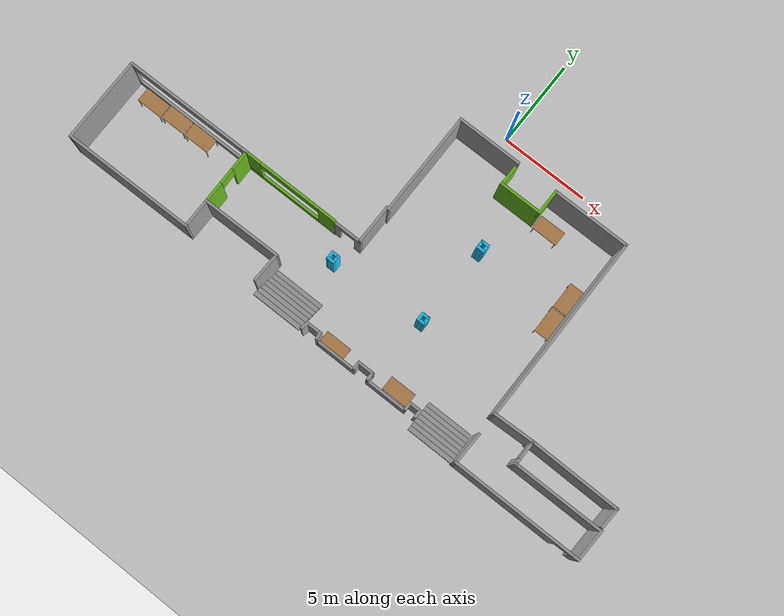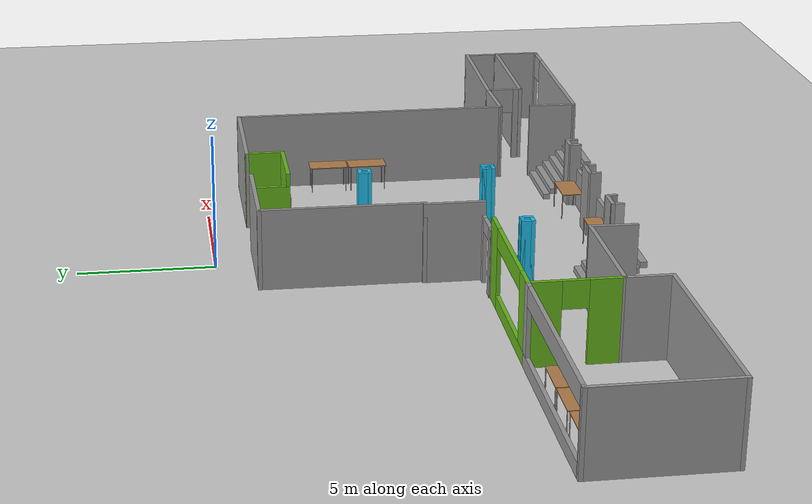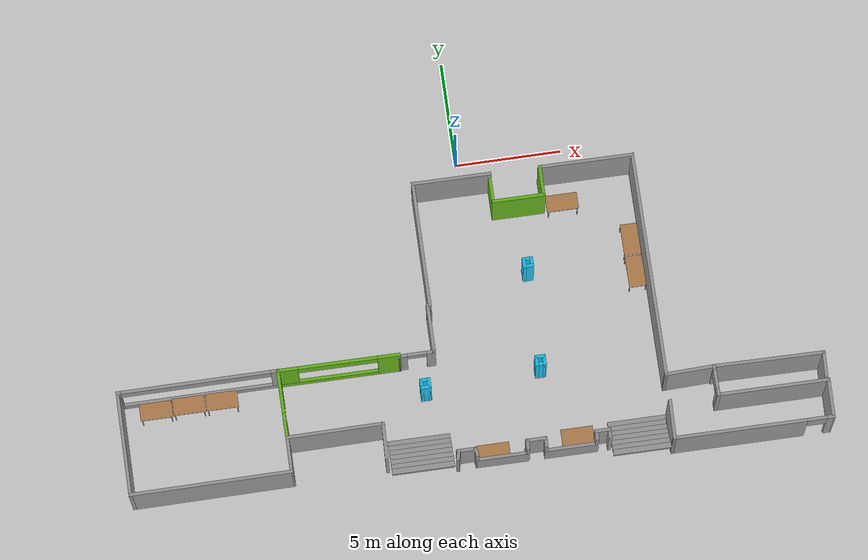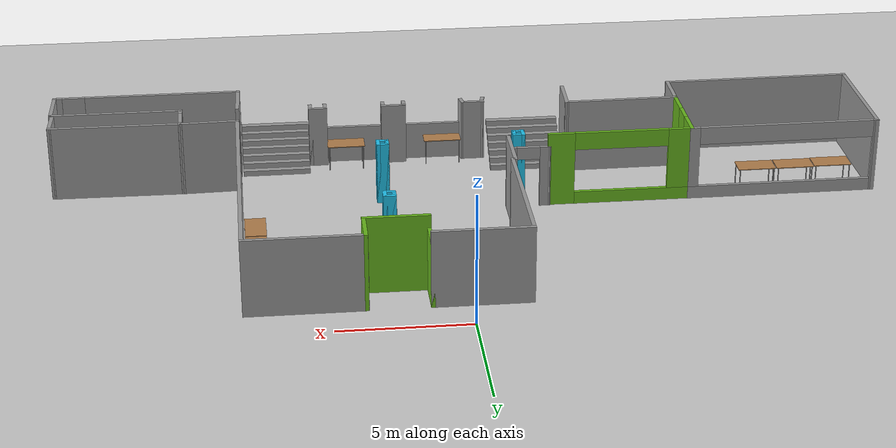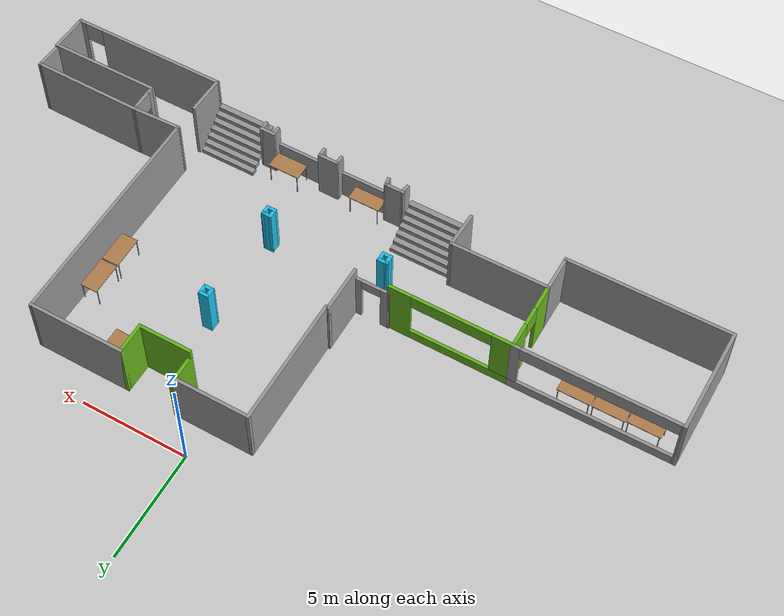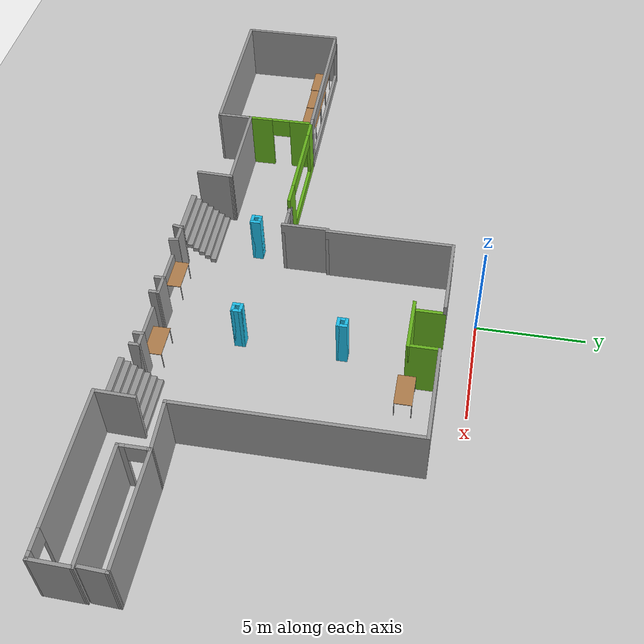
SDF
<sdf version="1.6">
 <world name="default">
  <light name="sun" type="directional">
   <pose>0 0 10 0 -0 0</pose>
   <diffuse>0.8 0.8 0.8 1</diffuse>
   <specular>0.1 0.1 0.1 1</specular>
   <attenuation>
    <range>1000</range>
    <constant>0.9</constant>
    <linear>0.01</linear>
    <quadratic>0.001</quadratic>
   </attenuation>
   <direction>-0.5 0.5 -1</direction>
  </light>
  <model name="ground_plane">
   <static>1</static>
   <link name="link">
    <collision name="collision">
     <geometry><plane><normal>0 0 1</normal><size>100 100</size></plane></geometry>
     <surface><friction><ode><mu>100</mu><mu2>50</mu2></ode></friction></surface>
    </collision>
    <visual name="visual">
     <cast_shadows>0</cast_shadows>
     <geometry><plane><normal>0 0 1</normal><size>100 100</size></plane></geometry>
     <material>
      <script><uri>file://media/materials/scripts/gazebo.material</uri><name>Gazebo/Grey</name></script>
     </material>
    </visual>
   </link>
  </model>
  <gravity>0 0 -9.8</gravity>
  <magnetic_field>6e-06 2.3e-05 -4.2e-05</magnetic_field>
  <atmosphere type="adiabatic"/>
  <physics name="default_physics" default="0" type="ode">
   <max_step_size>0.001</max_step_size>
   <real_time_factor>1</real_time_factor>
   <real_time_update_rate>1000</real_time_update_rate>
  </physics>
  <scene><ambient>0.4 0.4 0.4 1</ambient><background>0.7 0.7 0.7 1</background><shadows>1</shadows></scene>
  <spherical_coordinates>
   <surface_model>EARTH_WGS84</surface_model>
   <latitude_deg>0</latitude_deg>
   <longitude_deg>0</longitude_deg>
   <elevation>0</elevation>
   <heading_deg>0</heading_deg>
  </spherical_coordinates>
  <model name="digilabs">
   <pose>-0.7518 -8.27015 0 0 -0 0</pose>
   <link name="Stairs_4">
    <visual name="Stairs_4_Visual_0">
     <pose>-2.7433 -4.67133 0.106857 0 -0 0</pose>
     <geometry><box><size>2.91 0.265714 0.213714</size></box></geometry>
     <material>
      <script><uri>file://media/materials/scripts/gazebo.material</uri><name>Gazebo/Grey</name></script>
      <ambient>1 1 1 1</ambient>
     </material>
     <meta><layer>0</layer></meta>
    </visual>
    <collision name="Stairs_4_Collision_0">
     <geometry><box><size>2.91 0.265714 0.213714</size></box></geometry>
     <pose>-2.7433 -4.67133 0.106857 0 -0 0</pose>
    </collision>
    <visual name="Stairs_4_Visual_1">
     <pose>-2.7433 -4.93704 0.320571 0 -0 0</pose>
     <geometry><box><size>2.91 0.265714 0.213714</size></box></geometry>
     <material>
      <script><uri>file://media/materials/scripts/gazebo.material</uri><name>Gazebo/Grey</name></script>
      <ambient>1 1 1 1</ambient>
     </material>
     <meta><layer>0</layer></meta>
    </visual>
    <collision name="Stairs_4_Collision_1">
     <geometry><box><size>2.91 0.265714 0.213714</size></box></geometry>
     <pose>-2.7433 -4.93704 0.320571 0 -0 0</pose>
    </collision>
    <visual name="Stairs_4_Visual_2">
     <pose>-2.7433 -5.20275 0.534286 0 -0 0</pose>
     <geometry><box><size>2.91 0.265714 0.213714</size></box></geometry>
     <material>
      <script><uri>file://media/materials/scripts/gazebo.material</uri><name>Gazebo/Grey</name></script>
      <ambient>1 1 1 1</ambient>
     </material>
     <meta><layer>0</layer></meta>
    </visual>
    <collision name="Stairs_4_Collision_2">
     <geometry><box><size>2.91 0.265714 0.213714</size></box></geometry>
     <pose>-2.7433 -5.20275 0.534286 0 -0 0</pose>
    </collision>
    <visual name="Stairs_4_Visual_3">
     <pose>-2.7433 -5.46847 0.748 0 -0 0</pose>
     <geometry><box><size>2.91 0.265714 0.213714</size></box></geometry>
     <material>
      <script><uri>file://media/materials/scripts/gazebo.material</uri><name>Gazebo/Grey</name></script>
      <ambient>1 1 1 1</ambient>
     </material>
     <meta><layer>0</layer></meta>
    </visual>
    <collision name="Stairs_4_Collision_3">
     <geometry><box><size>2.91 0.265714 0.213714</size></box></geometry>
     <pose>-2.7433 -5.46847 0.748 0 -0 0</pose>
    </collision>
    <visual name="Stairs_4_Visual_4">
     <pose>-2.7433 -5.73418 0.961714 0 -0 0</pose>
     <geometry><box><size>2.91 0.265714 0.213714</size></box></geometry>
     <material>
      <script><uri>file://media/materials/scripts/gazebo.material</uri><name>Gazebo/Grey</name></script>
      <ambient>1 1 1 1</ambient>
     </material>
     <meta><layer>0</layer></meta>
    </visual>
    <collision name="Stairs_4_Collision_4">
     <geometry><box><size>2.91 0.265714 0.213714</size></box></geometry>
     <pose>-2.7433 -5.73418 0.961714 0 -0 0</pose>
    </collision>
    <visual name="Stairs_4_Visual_5">
     <pose>-2.7433 -5.9999 1.17543 0 -0 0</pose>
     <geometry><box><size>2.91 0.265714 0.213714</size></box></geometry>
     <material>
      <script><uri>file://media/materials/scripts/gazebo.material</uri><name>Gazebo/Grey</name></script>
      <ambient>1 1 1 1</ambient>
     </material>
     <meta><layer>0</layer></meta>
    </visual>
    <collision name="Stairs_4_Collision_5">
     <geometry><box><size>2.91 0.265714 0.213714</size></box></geometry>
     <pose>-2.7433 -5.9999 1.17543 0 -0 0</pose>
    </collision>
    <visual name="Stairs_4_Visual_6">
     <pose>-2.7433 -6.26561 1.38914 0 -0 0</pose>
     <geometry><box><size>2.91 0.265714 0.213714</size></box></geometry>
     <material>
      <script><uri>file://media/materials/scripts/gazebo.material</uri><name>Gazebo/Grey</name></script>
      <ambient>1 1 1 1</ambient>
     </material>
     <meta><layer>0</layer></meta>
    </visual>
    <collision name="Stairs_4_Collision_6">
     <geometry><box><size>2.91 0.265714 0.213714</size></box></geometry>
     <pose>-2.7433 -6.26561 1.38914 0 -0 0</pose>
    </collision>
   </link>
   <link name="Stairs_5">
    <visual name="Stairs_5_Visual_0">
     <pose>7.35413 -5.1708 0.107143 0 -0 0</pose>
     <geometry><box><size>2.688 0.265286 0.214286</size></box></geometry>
     <material>
      <script><uri>file://media/materials/scripts/gazebo.material</uri><name>Gazebo/Grey</name></script>
      <ambient>1 1 1 1</ambient>
     </material>
     <meta><layer>0</layer></meta>
    </visual>
    <collision name="Stairs_5_Collision_0">
     <geometry><box><size>2.688 0.265286 0.214286</size></box></geometry>
     <pose>7.35413 -5.1708 0.107143 0 -0 0</pose>
    </collision>
    <visual name="Stairs_5_Visual_1">
     <pose>7.35413 -5.43608 0.321429 0 -0 0</pose>
     <geometry><box><size>2.688 0.265286 0.214286</size></box></geometry>
     <material>
      <script><uri>file://media/materials/scripts/gazebo.material</uri><name>Gazebo/Grey</name></script>
      <ambient>1 1 1 1</ambient>
     </material>
     <meta><layer>0</layer></meta>
    </visual>
    <collision name="Stairs_5_Collision_1">
     <geometry><box><size>2.688 0.265286 0.214286</size></box></geometry>
     <pose>7.35413 -5.43608 0.321429 0 -0 0</pose>
    </collision>
    <visual name="Stairs_5_Visual_2">
     <pose>7.35413 -5.70137 0.535714 0 -0 0</pose>
     <geometry><box><size>2.688 0.265286 0.214286</size></box></geometry>
     <material>
      <script><uri>file://media/materials/scripts/gazebo.material</uri><name>Gazebo/Grey</name></script>
      <ambient>1 1 1 1</ambient>
     </material>
     <meta><layer>0</layer></meta>
    </visual>
    <collision name="Stairs_5_Collision_2">
     <geometry><box><size>2.688 0.265286 0.214286</size></box></geometry>
     <pose>7.35413 -5.70137 0.535714 0 -0 0</pose>
    </collision>
    <visual name="Stairs_5_Visual_3">
     <pose>7.35413 -5.96665 0.75 0 -0 0</pose>
     <geometry><box><size>2.688 0.265286 0.214286</size></box></geometry>
     <material>
      <script><uri>file://media/materials/scripts/gazebo.material</uri><name>Gazebo/Grey</name></script>
      <ambient>1 1 1 1</ambient>
     </material>
     <meta><layer>0</layer></meta>
    </visual>
    <collision name="Stairs_5_Collision_3">
     <geometry><box><size>2.688 0.265286 0.214286</size></box></geometry>
     <pose>7.35413 -5.96665 0.75 0 -0 0</pose>
    </collision>
    <visual name="Stairs_5_Visual_4">
     <pose>7.35413 -6.23194 0.964286 0 -0 0</pose>
     <geometry><box><size>2.688 0.265286 0.214286</size></box></geometry>
     <material>
      <script><uri>file://media/materials/scripts/gazebo.material</uri><name>Gazebo/Grey</name></script>
      <ambient>1 1 1 1</ambient>
     </material>
     <meta><layer>0</layer></meta>
    </visual>
    <collision name="Stairs_5_Collision_4">
     <geometry><box><size>2.688 0.265286 0.214286</size></box></geometry>
     <pose>7.35413 -6.23194 0.964286 0 -0 0</pose>
    </collision>
    <visual name="Stairs_5_Visual_5">
     <pose>7.35413 -6.49722 1.17857 0 -0 0</pose>
     <geometry><box><size>2.688 0.265286 0.214286</size></box></geometry>
     <material>
      <script><uri>file://media/materials/scripts/gazebo.material</uri><name>Gazebo/Grey</name></script>
      <ambient>1 1 1 1</ambient>
     </material>
     <meta><layer>0</layer></meta>
    </visual>
    <collision name="Stairs_5_Collision_5">
     <geometry><box><size>2.688 0.265286 0.214286</size></box></geometry>
     <pose>7.35413 -6.49722 1.17857 0 -0 0</pose>
    </collision>
    <visual name="Stairs_5_Visual_6">
     <pose>7.35413 -6.76251 1.39286 0 -0 0</pose>
     <geometry><box><size>2.688 0.265286 0.214286</size></box></geometry>
     <material>
      <script><uri>file://media/materials/scripts/gazebo.material</uri><name>Gazebo/Grey</name></script>
      <ambient>1 1 1 1</ambient>
     </material>
     <meta><layer>0</layer></meta>
    </visual>
    <collision name="Stairs_5_Collision_6">
     <geometry><box><size>2.688 0.265286 0.214286</size></box></geometry>
     <pose>7.35413 -6.76251 1.39286 0 -0 0</pose>
    </collision>
   </link>
   <link name="Wall_0">
    <collision name="Wall_0_Collision">
     <geometry><box><size>3.75 0.15 3</size></box></geometry>
     <pose>0 0 1.5 0 -0 0</pose>
    </collision>
    <visual name="Wall_0_Visual">
     <pose>0 0 1.5 0 -0 0</pose>
     <geometry><box><size>3.75 0.15 3</size></box></geometry>
     <material>
      <script><uri>file://media/materials/scripts/gazebo.material</uri><name>Gazebo/Grey</name></script>
      <ambient>1 1 1 1</ambient>
     </material>
     <meta><layer>0</layer></meta>
    </visual>
    <pose>0.3518 6.82015 0 0 -0 0</pose>
   </link>
   <link name="Wall_1">
    <collision name="Wall_1_Collision">
     <geometry><box><size>1.5 0.15 2.5</size></box></geometry>
     <pose>0 0 1.25 0 -0 0</pose>
    </collision>
    <visual name="Wall_1_Visual">
     <pose>0 0 1.25 0 -0 0</pose>
     <geometry><box><size>1.5 0.15 2.5</size></box></geometry>
     <material>
      <script><uri>file://media/materials/scripts/gazebo.material</uri><name>Gazebo/Grey</name></script>
      <ambient>0.403922 0.709804 0.113725 1</ambient>
     </material>
     <meta><layer>0</layer></meta>
    </visual>
    <pose>2.1518 6.14515 0 0 0 -1.5708</pose>
   </link>
   <link name="Wall_10">
    <pose>-2.3482 -1.12985 0 0 -0 3.14159</pose>
    <visual name="Wall_10_Visual_0">
     <pose>-0.667497 0 1.25 0 -0 0</pose>
     <geometry><box><size>0.415005 0.15 2.5</size></box></geometry>
     <material>
      <script><uri>file://media/materials/scripts/gazebo.material</uri><name>Gazebo/Grey</name></script>
      <ambient>1 1 1 1</ambient>
     </material>
     <meta><layer>0</layer></meta>
    </visual>
    <collision name="Wall_10_Collision_0">
     <geometry><box><size>0.415005 0.15 2.5</size></box></geometry>
     <pose>-0.667497 0 1.25 0 -0 0</pose>
    </collision>
    <visual name="Wall_10_Visual_1">
     <pose>0.657503 0 1.25 0 -0 0</pose>
     <geometry><box><size>0.434995 0.15 2.5</size></box></geometry>
     <material>
      <script><uri>file://media/materials/scripts/gazebo.material</uri><name>Gazebo/Grey</name></script>
      <ambient>1 1 1 1</ambient>
     </material>
     <meta><layer>0</layer></meta>
    </visual>
    <collision name="Wall_10_Collision_1">
     <geometry><box><size>0.434995 0.15 2.5</size></box></geometry>
     <pose>0.657503 0 1.25 0 -0 0</pose>
    </collision>
    <visual name="Wall_10_Visual_2">
     <pose>-0.009995 0 2.25 0 -0 0</pose>
     <geometry><box><size>0.9 0.15 0.5</size></box></geometry>
     <material>
      <script><uri>file://media/materials/scripts/gazebo.material</uri><name>Gazebo/Grey</name></script>
      <ambient>1 1 1 1</ambient>
     </material>
     <meta><layer>0</layer></meta>
    </visual>
    <collision name="Wall_10_Collision_2">
     <geometry><box><size>0.9 0.15 0.5</size></box></geometry>
     <pose>-0.009995 0 2.25 0 -0 0</pose>
    </collision>
   </link>
   <link name="Wall_11">
    <collision name="Wall_11_Collision">
     <geometry><box><size>0.19801 0.15 2.5</size></box></geometry>
     <pose>0 0 1.25 0 -0 0</pose>
    </collision>
    <visual name="Wall_11_Visual">
     <pose>0 0 1.25 0 -0 0</pose>
     <geometry><box><size>0.19801 0.15 2.5</size></box></geometry>
     <material>
      <script><uri>file://media/materials/scripts/gazebo.material</uri><name>Gazebo/Grey</name></script>
      <ambient>1 1 1 1</ambient>
     </material>
     <meta><layer>0</layer></meta>
    </visual>
    <pose>-3.1622 -1.14935 0 0 0 -2.19347</pose>
   </link>
   <link name="Wall_12">
    <pose>-5.9762 -1.16885 0 0 -0 3.14159</pose>
    <visual name="Wall_12_Visual_0">
     <pose>-2.34011 0 1.5 0 -0 0</pose>
     <geometry><box><size>1.06978 0.15 3</size></box></geometry>
     <material>
      <script><uri>file://media/materials/scripts/gazebo.material</uri><name>Gazebo/Grey</name></script>
      <ambient>0.403922 0.709804 0.113725 1</ambient>
     </material>
     <meta><layer>0</layer></meta>
    </visual>
    <collision name="Wall_12_Collision_0">
     <geometry><box><size>1.06978 0.15 3</size></box></geometry>
     <pose>-2.34011 0 1.5 0 -0 0</pose>
    </collision>
    <visual name="Wall_12_Visual_1">
     <pose>0.534892 0 0.25 0 -0 0</pose>
     <geometry><box><size>4.68022 0.15 0.5</size></box></geometry>
     <material>
      <script><uri>file://media/materials/scripts/gazebo.material</uri><name>Gazebo/Grey</name></script>
      <ambient>0.403922 0.709804 0.113725 1</ambient>
     </material>
     <meta><layer>0</layer></meta>
    </visual>
    <collision name="Wall_12_Collision_1">
     <geometry><box><size>4.68022 0.15 0.5</size></box></geometry>
     <pose>0.534892 0 0.25 0 -0 0</pose>
    </collision>
    <visual name="Wall_12_Visual_2">
     <pose>2.37639 0 1.75 0 -0 0</pose>
     <geometry><box><size>0.997216 0.15 2.5</size></box></geometry>
     <material>
      <script><uri>file://media/materials/scripts/gazebo.material</uri><name>Gazebo/Grey</name></script>
      <ambient>0.403922 0.709804 0.113725 1</ambient>
     </material>
     <meta><layer>0</layer></meta>
    </visual>
    <collision name="Wall_12_Collision_2">
     <geometry><box><size>0.997216 0.15 2.5</size></box></geometry>
     <pose>2.37639 0 1.75 0 -0 0</pose>
    </collision>
    <visual name="Wall_12_Visual_3">
     <pose>0.036284 0 2.65 0 -0 0</pose>
     <geometry><box><size>3.683 0.15 0.7</size></box></geometry>
     <material>
      <script><uri>file://media/materials/scripts/gazebo.material</uri><name>Gazebo/Grey</name></script>
      <ambient>0.403922 0.709804 0.113725 1</ambient>
     </material>
     <meta><layer>0</layer></meta>
    </visual>
    <collision name="Wall_12_Collision_3">
     <geometry><box><size>3.683 0.15 0.7</size></box></geometry>
     <pose>0.036284 0 2.65 0 -0 0</pose>
    </collision>
   </link>
   <link name="Wall_13">
    <pose>-8.7622 -2.74935 0 0 0 -1.56194</pose>
    <visual name="Wall_13_Visual_0">
     <pose>-1.06319 0 1.5 0 -0 0</pose>
     <geometry><box><size>1.18475 0.15 3</size></box></geometry>
     <material>
      <script><uri>file://media/materials/scripts/gazebo.material</uri><name>Gazebo/Grey</name></script>
      <ambient>0.403922 0.709804 0.113725 1</ambient>
     </material>
     <meta><layer>0</layer></meta>
    </visual>
    <collision name="Wall_13_Collision_0">
     <geometry><box><size>1.18475 0.15 3</size></box></geometry>
     <pose>-1.06319 0 1.5 0 -0 0</pose>
    </collision>
    <visual name="Wall_13_Visual_1">
     <pose>1.04238 0 1.5 0 -0 0</pose>
     <geometry><box><size>1.22637 0.15 3</size></box></geometry>
     <material>
      <script><uri>file://media/materials/scripts/gazebo.material</uri><name>Gazebo/Grey</name></script>
      <ambient>0.403922 0.709804 0.113725 1</ambient>
     </material>
     <meta><layer>0</layer></meta>
    </visual>
    <collision name="Wall_13_Collision_1">
     <geometry><box><size>1.22637 0.15 3</size></box></geometry>
     <pose>1.04238 0 1.5 0 -0 0</pose>
    </collision>
    <visual name="Wall_13_Visual_2">
     <pose>-0.020809 0 2.5 0 -0 0</pose>
     <geometry><box><size>0.9 0.15 1</size></box></geometry>
     <material>
      <script><uri>file://media/materials/scripts/gazebo.material</uri><name>Gazebo/Grey</name></script>
      <ambient>0.403922 0.709804 0.113725 1</ambient>
     </material>
     <meta><layer>0</layer></meta>
    </visual>
    <collision name="Wall_13_Collision_2">
     <geometry><box><size>0.9 0.15 1</size></box></geometry>
     <pose>-0.020809 0 2.5 0 -0 0</pose>
    </collision>
   </link>
   <link name="Wall_14">
    <collision name="Wall_14_Collision">
     <geometry><box><size>4.57641 0.15 3</size></box></geometry>
     <pose>0 0 1.5 0 -0 0</pose>
    </collision>
    <visual name="Wall_14_Visual">
     <pose>0 0 1.5 0 -0 0</pose>
     <geometry><box><size>4.57641 0.15 3</size></box></geometry>
     <material>
      <script><uri>file://media/materials/scripts/gazebo.material</uri><name>Gazebo/Grey</name></script>
      <ambient>1 1 1 1</ambient>
     </material>
     <meta><layer>0</layer></meta>
    </visual>
    <pose>-6.5352 -4.30885 0 0 -0 0.009489</pose>
   </link>
   <link name="Wall_15">
    <collision name="Wall_15_Collision">
     <geometry><box><size>1.75 0.15 3</size></box></geometry>
     <pose>0 0 1.5 0 -0 0</pose>
    </collision>
    <visual name="Wall_15_Visual">
     <pose>0 0 1.5 0 -0 0</pose>
     <geometry><box><size>1.75 0.15 3</size></box></geometry>
     <material>
      <script><uri>file://media/materials/scripts/gazebo.material</uri><name>Gazebo/Grey</name></script>
      <ambient>1 1 1 1</ambient>
     </material>
     <meta><layer>0</layer></meta>
    </visual>
    <pose>-4.3432 -5.08785 0 0 0 -1.59704</pose>
   </link>
   <link name="Wall_18">
    <collision name="Wall_18_Collision">
     <geometry><box><size>1.88877 0.15 3</size></box></geometry>
     <pose>0 0 1.5 0 -0 0</pose>
    </collision>
    <visual name="Wall_18_Visual">
     <pose>0 0 1.5 0 -0 0</pose>
     <geometry><box><size>1.88877 0.15 3</size></box></geometry>
     <material>
      <script><uri>file://media/materials/scripts/gazebo.material</uri><name>Gazebo/Grey</name></script>
      <ambient>1 1 1 1</ambient>
     </material>
     <meta><layer>0</layer></meta>
    </visual>
    <pose>8.8143 -5.92335 0 0 0 -1.59667</pose>
   </link>
   <link name="Wall_19">
    <pose>12.4668 -6.79285 0 0 -0 0</pose>
    <visual name="Wall_19_Visual_0">
     <pose>-0.640973 0 1.5 0 -0 0</pose>
     <geometry><box><size>6.21805 0.15 3</size></box></geometry>
     <material>
      <script><uri>file://media/materials/scripts/gazebo.material</uri><name>Gazebo/Grey</name></script>
      <ambient>1 1 1 1</ambient>
     </material>
     <meta><layer>0</layer></meta>
    </visual>
    <collision name="Wall_19_Collision_0">
     <geometry><box><size>6.21805 0.15 3</size></box></geometry>
     <pose>-0.640973 0 1.5 0 -0 0</pose>
    </collision>
    <visual name="Wall_19_Visual_1">
     <pose>3.55903 0 1.5 0 -0 0</pose>
     <geometry><box><size>0.381945 0.15 3</size></box></geometry>
     <material>
      <script><uri>file://media/materials/scripts/gazebo.material</uri><name>Gazebo/Grey</name></script>
      <ambient>1 1 1 1</ambient>
     </material>
     <meta><layer>0</layer></meta>
    </visual>
    <collision name="Wall_19_Collision_1">
     <geometry><box><size>0.381945 0.15 3</size></box></geometry>
     <pose>3.55903 0 1.5 0 -0 0</pose>
    </collision>
    <visual name="Wall_19_Visual_2">
     <pose>2.91805 0 2.5 0 -0 0</pose>
     <geometry><box><size>0.9 0.15 1</size></box></geometry>
     <material>
      <script><uri>file://media/materials/scripts/gazebo.material</uri><name>Gazebo/Grey</name></script>
      <ambient>1 1 1 1</ambient>
     </material>
     <meta><layer>0</layer></meta>
    </visual>
    <collision name="Wall_19_Collision_2">
     <geometry><box><size>0.9 0.15 1</size></box></geometry>
     <pose>2.91805 0 2.5 0 -0 0</pose>
    </collision>
   </link>
   <link name="Wall_2">
    <collision name="Wall_2_Collision">
     <geometry><box><size>2.5 0.15 3</size></box></geometry>
     <pose>0 0 1.5 0 -0 0</pose>
    </collision>
    <visual name="Wall_2_Visual">
     <pose>0 0 1.5 0 -0 0</pose>
     <geometry><box><size>2.5 0.15 3</size></box></geometry>
     <material>
      <script><uri>file://media/materials/scripts/gazebo.material</uri><name>Gazebo/Grey</name></script>
      <ambient>0.403922 0.709804 0.113725 1</ambient>
     </material>
     <meta><layer>0</layer></meta>
    </visual>
    <pose>3.3268 5.47015 0 0 -0 0</pose>
   </link>
   <link name="Wall_20">
    <collision name="Wall_20_Collision">
     <geometry><box><size>1.88877 0.15 3</size></box></geometry>
     <pose>0 0 1.5 0 -0 0</pose>
    </collision>
    <visual name="Wall_20_Visual">
     <pose>0 0 1.5 0 -0 0</pose>
     <geometry><box><size>1.88877 0.15 3</size></box></geometry>
     <material>
      <script><uri>file://media/materials/scripts/gazebo.material</uri><name>Gazebo/Grey</name></script>
      <ambient>1 1 1 1</ambient>
     </material>
     <meta><layer>0</layer></meta>
    </visual>
    <pose>16.1643 -5.92335 0 0 -0 1.54493</pose>
   </link>
   <link name="Wall_21">
    <collision name="Wall_21_Collision">
     <geometry><box><size>5.25 0.15 3</size></box></geometry>
     <pose>0 0 1.5 0 -0 0</pose>
    </collision>
    <visual name="Wall_21_Visual">
     <pose>0 0 1.5 0 -0 0</pose>
     <geometry><box><size>5.25 0.15 3</size></box></geometry>
     <material>
      <script><uri>file://media/materials/scripts/gazebo.material</uri><name>Gazebo/Grey</name></script>
      <ambient>1 1 1 1</ambient>
     </material>
     <meta><layer>0</layer></meta>
    </visual>
    <pose>13.6368 -5.05385 0 0 -0 3.14159</pose>
   </link>
   <link name="Wall_22">
    <pose>11.0868 -4.37885 0 0 -0 1.5708</pose>
    <visual name="Wall_22_Visual_0">
     <pose>-0.560049 0 1.5 0 -0 0</pose>
     <geometry><box><size>0.379903 0.15 3</size></box></geometry>
     <material>
      <script><uri>file://media/materials/scripts/gazebo.material</uri><name>Gazebo/Grey</name></script>
      <ambient>1 1 1 1</ambient>
     </material>
     <meta><layer>0</layer></meta>
    </visual>
    <collision name="Wall_22_Collision_0">
     <geometry><box><size>0.379903 0.15 3</size></box></geometry>
     <pose>-0.560049 0 1.5 0 -0 0</pose>
    </collision>
    <visual name="Wall_22_Visual_1">
     <pose>0.639951 0 1.5 0 -0 0</pose>
     <geometry><box><size>0.220097 0.15 3</size></box></geometry>
     <material>
      <script><uri>file://media/materials/scripts/gazebo.material</uri><name>Gazebo/Grey</name></script>
      <ambient>1 1 1 1</ambient>
     </material>
     <meta><layer>0</layer></meta>
    </visual>
    <collision name="Wall_22_Collision_1">
     <geometry><box><size>0.220097 0.15 3</size></box></geometry>
     <pose>0.639951 0 1.5 0 -0 0</pose>
    </collision>
    <visual name="Wall_22_Visual_2">
     <pose>0.079903 0 2.5 0 -0 0</pose>
     <geometry><box><size>0.9 0.15 1</size></box></geometry>
     <material>
      <script><uri>file://media/materials/scripts/gazebo.material</uri><name>Gazebo/Grey</name></script>
      <ambient>1 1 1 1</ambient>
     </material>
     <meta><layer>0</layer></meta>
    </visual>
    <collision name="Wall_22_Collision_2">
     <geometry><box><size>0.9 0.15 1</size></box></geometry>
     <pose>0.079903 0 2.5 0 -0 0</pose>
    </collision>
   </link>
   <link name="Wall_23">
    <collision name="Wall_23_Collision">
     <geometry><box><size>5.22834 0.15 3</size></box></geometry>
     <pose>0 0 1.5 0 -0 0</pose>
    </collision>
    <visual name="Wall_23_Visual">
     <pose>0 0 1.5 0 -0 0</pose>
     <geometry><box><size>5.22834 0.15 3</size></box></geometry>
     <material>
      <script><uri>file://media/materials/scripts/gazebo.material</uri><name>Gazebo/Grey</name></script>
      <ambient>1 1 1 1</ambient>
     </material>
     <meta><layer>0</layer></meta>
    </visual>
    <pose>13.6258 -3.72685 0 0 0 -0.009058</pose>
   </link>
   <link name="Wall_24">
    <collision name="Wall_24_Collision">
     <geometry><box><size>1.25 0.15 3</size></box></geometry>
     <pose>0 0 1.5 0 -0 0</pose>
    </collision>
    <visual name="Wall_24_Visual">
     <pose>0 0 1.5 0 -0 0</pose>
     <geometry><box><size>1.25 0.15 3</size></box></geometry>
     <material>
      <script><uri>file://media/materials/scripts/gazebo.material</uri><name>Gazebo/Grey</name></script>
      <ambient>1 1 1 1</ambient>
     </material>
     <meta><layer>0</layer></meta>
    </visual>
    <pose>16.1423 -4.29985 0 0 0 -1.61168</pose>
   </link>
   <link name="Wall_26">
    <collision name="Wall_26_Collision">
     <geometry><box><size>2.38646 0.15 3</size></box></geometry>
     <pose>0 0 1.5 0 -0 0</pose>
    </collision>
    <visual name="Wall_26_Visual">
     <pose>0 0 1.5 0 -0 0</pose>
     <geometry><box><size>2.38646 0.15 3</size></box></geometry>
     <material>
      <script><uri>file://media/materials/scripts/gazebo.material</uri><name>Gazebo/Grey</name></script>
      <ambient>1 1 1 1</ambient>
     </material>
     <meta><layer>0</layer></meta>
    </visual>
    <pose>9.9693 -3.74185 0 0 0 -3.1076</pose>
   </link>
   <link name="Wall_28">
    <collision name="Wall_28_Collision">
     <geometry><box><size>0.75 0.15 2.5</size></box></geometry>
     <pose>0 0 1.25 0 -0 0</pose>
    </collision>
    <visual name="Wall_28_Visual">
     <pose>0 0 1.25 0 -0 0</pose>
     <geometry><box><size>0.75 0.15 2.5</size></box></geometry>
     <material>
      <script><uri>file://media/materials/scripts/gazebo.material</uri><name>Gazebo/Grey</name></script>
      <ambient>1 1 1 1</ambient>
     </material>
     <meta><layer>0</layer></meta>
    </visual>
    <pose>5.6169 -5.8754 0 0 -0 3.14159</pose>
   </link>
   <link name="Wall_3">
    <collision name="Wall_3_Collision">
     <geometry><box><size>1.5 0.15 3</size></box></geometry>
     <pose>0 0 1.5 0 -0 0</pose>
    </collision>
    <visual name="Wall_3_Visual">
     <pose>0 0 1.5 0 -0 0</pose>
     <geometry><box><size>1.5 0.15 3</size></box></geometry>
     <material>
      <script><uri>file://media/materials/scripts/gazebo.material</uri><name>Gazebo/Grey</name></script>
      <ambient>0.403922 0.709804 0.113725 1</ambient>
     </material>
     <meta><layer>0</layer></meta>
    </visual>
    <pose>4.5018 6.14515 0 0 -0 1.5708</pose>
   </link>
   <link name="Wall_4">
    <collision name="Wall_4_Collision">
     <geometry><box><size>4.5 0.15 3</size></box></geometry>
     <pose>0 0 1.5 0 -0 0</pose>
    </collision>
    <visual name="Wall_4_Visual">
     <pose>0 0 1.5 0 -0 0</pose>
     <geometry><box><size>4.5 0.15 3</size></box></geometry>
     <material>
      <script><uri>file://media/materials/scripts/gazebo.material</uri><name>Gazebo/Grey</name></script>
      <ambient>1 1 1 1</ambient>
     </material>
     <meta><layer>0</layer></meta>
    </visual>
    <pose>6.6768 6.82015 0 0 -0 0</pose>
   </link>
   <link name="Wall_42">
    <collision name="Wall_42_Collision">
     <geometry><box><size>0.5 0.15 2.5</size></box></geometry>
     <pose>0 0 1.25 0 -0 0</pose>
    </collision>
    <visual name="Wall_42_Visual">
     <pose>0 0 1.25 0 -0 0</pose>
     <geometry><box><size>0.5 0.15 2.5</size></box></geometry>
     <material>
      <script><uri>file://media/materials/scripts/gazebo.material</uri><name>Gazebo/Grey</name></script>
      <ambient>0.121569 0.764706 0.92549 1</ambient>
     </material>
     <meta><layer>0</layer></meta>
    </visual>
    <pose>3.34428 2.66264 0 0 -0 0</pose>
   </link>
   <link name="Wall_43">
    <collision name="Wall_43_Collision">
     <geometry><box><size>0.5 0.15 2.5</size></box></geometry>
     <pose>0 0 1.25 0 -0 0</pose>
    </collision>
    <visual name="Wall_43_Visual">
     <pose>0 0 1.25 0 -0 0</pose>
     <geometry><box><size>0.5 0.15 2.5</size></box></geometry>
     <material>
      <script><uri>file://media/materials/scripts/gazebo.material</uri><name>Gazebo/Grey</name></script>
      <ambient>0.12549 0.764706 0.941176 1</ambient>
     </material>
     <meta><layer>0</layer></meta>
    </visual>
    <pose>3.51928 2.48764 0 0 0 -1.5708</pose>
   </link>
   <link name="Wall_44">
    <collision name="Wall_44_Collision">
     <geometry><box><size>0.5 0.15 2.5</size></box></geometry>
     <pose>0 0 1.25 0 -0 0</pose>
    </collision>
    <visual name="Wall_44_Visual">
     <pose>0 0 1.25 0 -0 0</pose>
     <geometry><box><size>0.5 0.15 2.5</size></box></geometry>
     <material>
      <script><uri>file://media/materials/scripts/gazebo.material</uri><name>Gazebo/Grey</name></script>
      <ambient>0.12549 0.764706 0.941176 1</ambient>
     </material>
     <meta><layer>0</layer></meta>
    </visual>
    <pose>3.34428 2.31264 0 0 -0 3.14159</pose>
   </link>
   <link name="Wall_45">
    <collision name="Wall_45_Collision">
     <geometry><box><size>0.5 0.15 2.5</size></box></geometry>
     <pose>0 0 1.25 0 -0 0</pose>
    </collision>
    <visual name="Wall_45_Visual">
     <pose>0 0 1.25 0 -0 0</pose>
     <geometry><box><size>0.5 0.15 2.5</size></box></geometry>
     <material>
      <script><uri>file://media/materials/scripts/gazebo.material</uri><name>Gazebo/Grey</name></script>
      <ambient>0.12549 0.764706 0.941176 1</ambient>
     </material>
     <meta><layer>0</layer></meta>
    </visual>
    <pose>3.16928 2.48764 0 0 -0 1.5708</pose>
   </link>
   <link name="Wall_47">
    <collision name="Wall_47_Collision">
     <geometry><box><size>0.5 0.15 2.5</size></box></geometry>
     <pose>0 0 1.25 0 -0 0</pose>
    </collision>
    <visual name="Wall_47_Visual">
     <pose>0 0 1.25 0 -0 0</pose>
     <geometry><box><size>0.5 0.15 2.5</size></box></geometry>
     <material>
      <script><uri>file://media/materials/scripts/gazebo.material</uri><name>Gazebo/Grey</name></script>
      <ambient>0.121569 0.764706 0.92549 1</ambient>
     </material>
     <meta><layer>0</layer></meta>
    </visual>
    <pose>3.25948 -2.02947 0 0 -0 0</pose>
   </link>
   <link name="Wall_48">
    <collision name="Wall_48_Collision">
     <geometry><box><size>0.5 0.15 2.5</size></box></geometry>
     <pose>0 0 1.25 0 -0 0</pose>
    </collision>
    <visual name="Wall_48_Visual">
     <pose>0 0 1.25 0 -0 0</pose>
     <geometry><box><size>0.5 0.15 2.5</size></box></geometry>
     <material>
      <script><uri>file://media/materials/scripts/gazebo.material</uri><name>Gazebo/Grey</name></script>
      <ambient>0.12549 0.764706 0.941176 1</ambient>
     </material>
     <meta><layer>0</layer></meta>
    </visual>
    <pose>3.43448 -2.20447 0 0 0 -1.5708</pose>
   </link>
   <link name="Wall_49">
    <collision name="Wall_49_Collision">
     <geometry><box><size>0.5 0.15 2.5</size></box></geometry>
     <pose>0 0 1.25 0 -0 0</pose>
    </collision>
    <visual name="Wall_49_Visual">
     <pose>0 0 1.25 0 -0 0</pose>
     <geometry><box><size>0.5 0.15 2.5</size></box></geometry>
     <material>
      <script><uri>file://media/materials/scripts/gazebo.material</uri><name>Gazebo/Grey</name></script>
      <ambient>0.12549 0.764706 0.941176 1</ambient>
     </material>
     <meta><layer>0</layer></meta>
    </visual>
    <pose>3.25948 -2.37947 0 0 -0 3.14159</pose>
   </link>
   <link name="Wall_5">
    <collision name="Wall_5_Collision">
     <geometry><box><size>10.75 0.15 3</size></box></geometry>
     <pose>0 0 1.5 0 -0 0</pose>
    </collision>
    <visual name="Wall_5_Visual">
     <pose>0 0 1.5 0 -0 0</pose>
     <geometry><box><size>10.75 0.15 3</size></box></geometry>
     <material>
      <script><uri>file://media/materials/scripts/gazebo.material</uri><name>Gazebo/Grey</name></script>
      <ambient>1 1 1 1</ambient>
     </material>
     <meta><layer>0</layer></meta>
    </visual>
    <pose>8.8518 1.52015 0 0 0 -1.5708</pose>
   </link>
   <link name="Wall_50">
    <collision name="Wall_50_Collision">
     <geometry><box><size>0.5 0.15 2.5</size></box></geometry>
     <pose>0 0 1.25 0 -0 0</pose>
    </collision>
    <visual name="Wall_50_Visual">
     <pose>0 0 1.25 0 -0 0</pose>
     <geometry><box><size>0.5 0.15 2.5</size></box></geometry>
     <material>
      <script><uri>file://media/materials/scripts/gazebo.material</uri><name>Gazebo/Grey</name></script>
      <ambient>0.121569 0.764706 0.92549 1</ambient>
     </material>
     <meta><layer>0</layer></meta>
    </visual>
    <pose>3.08448 -2.20447 0 0 -0 1.5708</pose>
   </link>
   <link name="Wall_52">
    <collision name="Wall_52_Collision">
     <geometry><box><size>0.5 0.15 2.5</size></box></geometry>
     <pose>0 0 1.25 0 -0 0</pose>
    </collision>
    <visual name="Wall_52_Visual">
     <pose>0 0 1.25 0 -0 0</pose>
     <geometry><box><size>0.5 0.15 2.5</size></box></geometry>
     <material>
      <script><uri>file://media/materials/scripts/gazebo.material</uri><name>Gazebo/Grey</name></script>
      <ambient>0.121569 0.764706 0.92549 1</ambient>
     </material>
     <meta><layer>0</layer></meta>
    </visual>
    <pose>-2.13927 -2.39692 0 0 -0 0</pose>
   </link>
   <link name="Wall_53">
    <collision name="Wall_53_Collision">
     <geometry><box><size>0.5 0.15 2.5</size></box></geometry>
     <pose>0 0 1.25 0 -0 0</pose>
    </collision>
    <visual name="Wall_53_Visual">
     <pose>0 0 1.25 0 -0 0</pose>
     <geometry><box><size>0.5 0.15 2.5</size></box></geometry>
     <material>
      <script><uri>file://media/materials/scripts/gazebo.material</uri><name>Gazebo/Grey</name></script>
      <ambient>0.12549 0.764706 0.941176 1</ambient>
     </material>
     <meta><layer>0</layer></meta>
    </visual>
    <pose>-1.96427 -2.57192 0 0 0 -1.5708</pose>
   </link>
   <link name="Wall_54">
    <collision name="Wall_54_Collision">
     <geometry><box><size>0.5 0.15 2.5</size></box></geometry>
     <pose>0 0 1.25 0 -0 0</pose>
    </collision>
    <visual name="Wall_54_Visual">
     <pose>0 0 1.25 0 -0 0</pose>
     <geometry><box><size>0.5 0.15 2.5</size></box></geometry>
     <material>
      <script><uri>file://media/materials/scripts/gazebo.material</uri><name>Gazebo/Grey</name></script>
      <ambient>0.12549 0.764706 0.941176 1</ambient>
     </material>
     <meta><layer>0</layer></meta>
    </visual>
    <pose>-2.13927 -2.74692 0 0 -0 3.14159</pose>
   </link>
   <link name="Wall_55">
    <collision name="Wall_55_Collision">
     <geometry><box><size>0.5 0.15 2.5</size></box></geometry>
     <pose>0 0 1.25 0 -0 0</pose>
    </collision>
    <visual name="Wall_55_Visual">
     <pose>0 0 1.25 0 -0 0</pose>
     <geometry><box><size>0.5 0.15 2.5</size></box></geometry>
     <material>
      <script><uri>file://media/materials/scripts/gazebo.material</uri><name>Gazebo/Grey</name></script>
      <ambient>0.121569 0.764706 0.92549 1</ambient>
     </material>
     <meta><layer>0</layer></meta>
    </visual>
    <pose>-2.31427 -2.57192 0 0 -0 1.5708</pose>
   </link>
   <link name="Wall_61">
    <collision name="Wall_61_Collision">
     <geometry><box><size>1.75 0.15 3</size></box></geometry>
     <pose>0 0 1.5 0 -0 0</pose>
    </collision>
    <visual name="Wall_61_Visual">
     <pose>0 0 1.5 0 -0 0</pose>
     <geometry><box><size>1.75 0.15 3</size></box></geometry>
     <material>
      <script><uri>file://media/materials/scripts/gazebo.material</uri><name>Gazebo/Grey</name></script>
      <ambient>1 1 1 1</ambient>
     </material>
     <meta><layer>0</layer></meta>
    </visual>
    <pose>-8.7482 -5.12985 0 0 0 -1.5708</pose>
   </link>
   <link name="Wall_62">
    <collision name="Wall_62_Collision">
     <geometry><box><size>7.56279 0.15 3</size></box></geometry>
     <pose>0 0 1.5 0 -0 0</pose>
    </collision>
    <visual name="Wall_62_Visual">
     <pose>0 0 1.5 0 -0 0</pose>
     <geometry><box><size>7.56279 0.15 3</size></box></geometry>
     <material>
      <script><uri>file://media/materials/scripts/gazebo.material</uri><name>Gazebo/Grey</name></script>
      <ambient>1 1 1 1</ambient>
     </material>
     <meta><layer>0</layer></meta>
    </visual>
    <pose>-12.4542 -5.96235 0 0 0 -3.13282</pose>
   </link>
   <link name="Wall_63">
    <collision name="Wall_63_Collision">
     <geometry><box><size>4.94794 0.15 3</size></box></geometry>
     <pose>0 0 1.5 0 -0 0</pose>
    </collision>
    <visual name="Wall_63_Visual">
     <pose>0 0 1.5 0 -0 0</pose>
     <geometry><box><size>4.94794 0.15 3</size></box></geometry>
     <material>
      <script><uri>file://media/materials/scripts/gazebo.material</uri><name>Gazebo/Grey</name></script>
      <ambient>1 1 1 1</ambient>
     </material>
     <meta><layer>0</layer></meta>
    </visual>
    <pose>-16.1742 -3.59635 0 0 -0 1.57663</pose>
   </link>
   <link name="Wall_64">
    <pose>-12.4822 -1.17885 0 0 -0 0.005127</pose>
    <visual name="Wall_64_Visual_0">
     <pose>-3.67349 0 1.5 0 -0 0</pose>
     <geometry><box><size>0.215363 0.15 3</size></box></geometry>
     <material>
      <script><uri>file://media/materials/scripts/gazebo.material</uri><name>Gazebo/Grey</name></script>
      <ambient>1 1 1 1</ambient>
     </material>
     <meta><layer>0</layer></meta>
    </visual>
    <collision name="Wall_64_Collision_0">
     <geometry><box><size>0.215363 0.15 3</size></box></geometry>
     <pose>-3.67349 0 1.5 0 -0 0</pose>
    </collision>
    <visual name="Wall_64_Visual_1">
     <pose>0.107681 0 0.25 0 -0 0</pose>
     <geometry><box><size>7.34698 0.15 0.5</size></box></geometry>
     <material>
      <script><uri>file://media/materials/scripts/gazebo.material</uri><name>Gazebo/Grey</name></script>
      <ambient>1 1 1 1</ambient>
     </material>
     <meta><layer>0</layer></meta>
    </visual>
    <collision name="Wall_64_Collision_1">
     <geometry><box><size>7.34698 0.15 0.5</size></box></geometry>
     <pose>0.107681 0 0.25 0 -0 0</pose>
    </collision>
    <visual name="Wall_64_Visual_2">
     <pose>3.57468 0 1.75 0 -0 0</pose>
     <geometry><box><size>0.412978 0.15 2.5</size></box></geometry>
     <material>
      <script><uri>file://media/materials/scripts/gazebo.material</uri><name>Gazebo/Grey</name></script>
      <ambient>1 1 1 1</ambient>
     </material>
     <meta><layer>0</layer></meta>
    </visual>
    <collision name="Wall_64_Collision_2">
     <geometry><box><size>0.412978 0.15 2.5</size></box></geometry>
     <pose>3.57468 0 1.75 0 -0 0</pose>
    </collision>
    <visual name="Wall_64_Visual_3">
     <pose>-0.098808 0 2.65 0 -0 0</pose>
     <geometry><box><size>6.934 0.15 0.7</size></box></geometry>
     <material>
      <script><uri>file://media/materials/scripts/gazebo.material</uri><name>Gazebo/Grey</name></script>
      <ambient>1 1 1 1</ambient>
     </material>
     <meta><layer>0</layer></meta>
    </visual>
    <collision name="Wall_64_Collision_3">
     <geometry><box><size>6.934 0.15 0.7</size></box></geometry>
     <pose>-0.098808 0 2.65 0 -0 0</pose>
    </collision>
   </link>
   <link name="Wall_67">
    <collision name="Wall_67_Collision">
     <geometry><box><size>0.5 0.15 2.5</size></box></geometry>
     <pose>0 0 1.25 0 -0 0</pose>
    </collision>
    <visual name="Wall_67_Visual">
     <pose>0 0 1.25 0 -0 0</pose>
     <geometry><box><size>0.5 0.15 2.5</size></box></geometry>
     <material>
      <script><uri>file://media/materials/scripts/gazebo.material</uri><name>Gazebo/Grey</name></script>
      <ambient>1 1 1 1</ambient>
     </material>
     <meta><layer>0</layer></meta>
    </visual>
    <pose>5.31685 -6.05062 0 0 0 -1.57108</pose>
   </link>
   <link name="Wall_68">
    <collision name="Wall_68_Collision">
     <geometry><box><size>2.50037 0.15 1.5</size></box></geometry>
     <pose>0 0 0.75 0 -0 0</pose>
    </collision>
    <visual name="Wall_68_Visual">
     <pose>0 0 0.75 0 -0 0</pose>
     <geometry><box><size>2.50037 0.15 1.5</size></box></geometry>
     <material>
      <script><uri>file://media/materials/scripts/gazebo.material</uri><name>Gazebo/Grey</name></script>
      <ambient>1 1 1 1</ambient>
     </material>
     <meta><layer>0</layer></meta>
    </visual>
    <pose>4.1418 -6.22585 0 0 -0 3.14159</pose>
   </link>
   <link name="Wall_7">
    <collision name="Wall_7_Collision">
     <geometry><box><size>6 0.15 3</size></box></geometry>
     <pose>0 0 1.5 0 -0 0</pose>
    </collision>
    <visual name="Wall_7_Visual">
     <pose>0 0 1.5 0 -0 0</pose>
     <geometry><box><size>6 0.15 3</size></box></geometry>
     <material>
      <script><uri>file://media/materials/scripts/gazebo.material</uri><name>Gazebo/Grey</name></script>
      <ambient>1 1 1 1</ambient>
     </material>
     <meta><layer>0</layer></meta>
    </visual>
    <pose>-1.4482 3.89515 0 0 0 -1.5708</pose>
   </link>
   <link name="Wall_75">
    <collision name="Wall_75_Collision">
     <geometry><box><size>0.5 0.15 2.5</size></box></geometry>
     <pose>0 0 1.25 0 -0 0</pose>
    </collision>
    <visual name="Wall_75_Visual">
     <pose>0 0 1.25 0 -0 0</pose>
     <geometry><box><size>0.5 0.15 2.5</size></box></geometry>
     <material>
      <script><uri>file://media/materials/scripts/gazebo.material</uri><name>Gazebo/Grey</name></script>
      <ambient>1 1 1 1</ambient>
     </material>
     <meta><layer>0</layer></meta>
    </visual>
    <pose>2.96685 -6.05062 0 0 -0 1.57051</pose>
   </link>
   <link name="Wall_76">
    <collision name="Wall_76_Collision">
     <geometry><box><size>1 0.15 2.5</size></box></geometry>
     <pose>0 0 1.25 0 -0 0</pose>
    </collision>
    <visual name="Wall_76_Visual">
     <pose>0 0 1.25 0 -0 0</pose>
     <geometry><box><size>1 0.15 2.5</size></box></geometry>
     <material>
      <script><uri>file://media/materials/scripts/gazebo.material</uri><name>Gazebo/Grey</name></script>
      <ambient>1 1 1 1</ambient>
     </material>
     <meta><layer>0</layer></meta>
    </visual>
    <pose>2.5419 -5.8754 0 0 -0 3.14159</pose>
   </link>
   <link name="Wall_77">
    <collision name="Wall_77_Collision">
     <geometry><box><size>0.5 0.15 2.5</size></box></geometry>
     <pose>0 0 1.25 0 -0 0</pose>
    </collision>
    <visual name="Wall_77_Visual">
     <pose>0 0 1.25 0 -0 0</pose>
     <geometry><box><size>0.5 0.15 2.5</size></box></geometry>
     <material>
      <script><uri>file://media/materials/scripts/gazebo.material</uri><name>Gazebo/Grey</name></script>
      <ambient>1 1 1 1</ambient>
     </material>
     <meta><layer>0</layer></meta>
    </visual>
    <pose>2.11685 -6.05062 0 0 0 -1.57108</pose>
   </link>
   <link name="Wall_78">
    <collision name="Wall_78_Collision">
     <geometry><box><size>2.5 0.15 1.5</size></box></geometry>
     <pose>0 0 0.75 0 -0 0</pose>
    </collision>
    <visual name="Wall_78_Visual">
     <pose>0 0 0.75 0 -0 0</pose>
     <geometry><box><size>2.5 0.15 1.5</size></box></geometry>
     <material>
      <script><uri>file://media/materials/scripts/gazebo.material</uri><name>Gazebo/Grey</name></script>
      <ambient>1 1 1 1</ambient>
     </material>
     <meta><layer>0</layer></meta>
    </visual>
    <pose>0.9418 -6.22585 0 0 -0 3.14159</pose>
   </link>
   <link name="Wall_79">
    <collision name="Wall_79_Collision">
     <geometry><box><size>0.457082 0.15 2.5</size></box></geometry>
     <pose>0 0 1.25 0 -0 0</pose>
    </collision>
    <visual name="Wall_79_Visual">
     <pose>0 0 1.25 0 -0 0</pose>
     <geometry><box><size>0.457082 0.15 2.5</size></box></geometry>
     <material>
      <script><uri>file://media/materials/scripts/gazebo.material</uri><name>Gazebo/Grey</name></script>
      <ambient>1 1 1 1</ambient>
     </material>
     <meta><layer>0</layer></meta>
    </visual>
    <pose>-0.257768 -6.07407 0 0 -0 1.73127</pose>
   </link>
   <link name="Wall_8">
    <collision name="Wall_8_Collision">
     <geometry><box><size>0.25 0.15 2.5</size></box></geometry>
     <pose>0 0 1.25 0 -0 0</pose>
    </collision>
    <visual name="Wall_8_Visual">
     <pose>0 0 1.25 0 -0 0</pose>
     <geometry><box><size>0.25 0.15 2.5</size></box></geometry>
     <material>
      <script><uri>file://media/materials/scripts/gazebo.material</uri><name>Gazebo/Grey</name></script>
      <ambient>1 1 1 1</ambient>
     </material>
     <meta><layer>0</layer></meta>
    </visual>
    <pose>-1.4982 0.970152 0 0 -0 3.14159</pose>
   </link>
   <link name="Wall_80">
    <collision name="Wall_80_Collision">
     <geometry><box><size>0.917685 0.15 2.5</size></box></geometry>
     <pose>0 0 1.25 0 -0 0</pose>
    </collision>
    <visual name="Wall_80_Visual">
     <pose>0 0 1.25 0 -0 0</pose>
     <geometry><box><size>0.917685 0.15 2.5</size></box></geometry>
     <material>
      <script><uri>file://media/materials/scripts/gazebo.material</uri><name>Gazebo/Grey</name></script>
      <ambient>1 1 1 1</ambient>
     </material>
     <meta><layer>0</layer></meta>
    </visual>
    <pose>-0.7081 -5.92229 0 0 -0 3.14159</pose>
   </link>
   <link name="Wall_81">
    <collision name="Wall_81_Collision">
     <geometry><box><size>0.509902 0.15 2.5</size></box></geometry>
     <pose>0 0 1.25 0 -0 0</pose>
    </collision>
    <visual name="Wall_81_Visual">
     <pose>0 0 1.25 0 -0 0</pose>
     <geometry><box><size>0.509902 0.15 2.5</size></box></geometry>
     <material>
      <script><uri>file://media/materials/scripts/gazebo.material</uri><name>Gazebo/Grey</name></script>
      <ambient>1 1 1 1</ambient>
     </material>
     <meta><layer>0</layer></meta>
    </visual>
    <pose>-1.09194 -6.09729 0 0 0 -1.80591</pose>
   </link>
   <link name="Wall_83">
    <collision name="Wall_83_Collision">
     <geometry><box><size>0.5 0.15 2.5</size></box></geometry>
     <pose>0 0 1.25 0 -0 0</pose>
    </collision>
    <visual name="Wall_83_Visual">
     <pose>0 0 1.25 0 -0 0</pose>
     <geometry><box><size>0.5 0.15 2.5</size></box></geometry>
     <material>
      <script><uri>file://media/materials/scripts/gazebo.material</uri><name>Gazebo/Grey</name></script>
      <ambient>1 1 1 1</ambient>
     </material>
     <meta><layer>0</layer></meta>
    </visual>
    <pose>5.9169 -6.0504 0 0 0 -1.5708</pose>
   </link>
   <link name="Wall_9">
    <collision name="Wall_9_Collision">
     <geometry><box><size>2.25 0.15 3</size></box></geometry>
     <pose>0 0 1.5 0 -0 0</pose>
    </collision>
    <visual name="Wall_9_Visual">
     <pose>0 0 1.5 0 -0 0</pose>
     <geometry><box><size>2.25 0.15 3</size></box></geometry>
     <material>
      <script><uri>file://media/materials/scripts/gazebo.material</uri><name>Gazebo/Grey</name></script>
      <ambient>1 1 1 1</ambient>
     </material>
     <meta><layer>0</layer></meta>
    </visual>
    <pose>-1.5482 -0.079848 0 0 0 -1.5708</pose>
   </link>
   <static>1</static>
  </model>
  <model name="table">
   <static>1</static>
   <link name="link">
    <collision name="surface">
     <pose>0 0 1 0 -0 0</pose>
     <geometry><box><size>1.5 0.8 0.03</size></box></geometry>
     <surface><friction><ode><mu>0.6</mu><mu2>0.6</mu2></ode></friction></surface>
    </collision>
    <visual name="visual1">
     <pose>0 0 1 0 -0 0</pose>
     <geometry><box><size>1.5 0.8 0.03</size></box></geometry>
     <material>
      <script><uri>file://media/materials/scripts/gazebo.material</uri><name>Gazebo/Wood</name></script>
     </material>
    </visual>
    <collision name="front_left_leg">
     <pose>0.68 0.38 0.5 0 -0 0</pose>
     <geometry><cylinder><radius>0.02</radius><length>1</length></cylinder></geometry>
    </collision>
    <visual name="front_left_leg">
     <pose>0.68 0.38 0.5 0 -0 0</pose>
     <geometry><cylinder><radius>0.02</radius><length>1</length></cylinder></geometry>
     <material>
      <script><uri>file://media/materials/scripts/gazebo.material</uri><name>Gazebo/Grey</name></script>
     </material>
    </visual>
    <collision name="front_right_leg">
     <pose>0.68 -0.38 0.5 0 -0 0</pose>
     <geometry><cylinder><radius>0.02</radius><length>1</length></cylinder></geometry>
    </collision>
    <visual name="front_right_leg">
     <pose>0.68 -0.38 0.5 0 -0 0</pose>
     <geometry><cylinder><radius>0.02</radius><length>1</length></cylinder></geometry>
     <material>
      <script><uri>file://media/materials/scripts/gazebo.material</uri><name>Gazebo/Grey</name></script>
     </material>
    </visual>
    <collision name="back_right_leg">
     <pose>-0.68 -0.38 0.5 0 -0 0</pose>
     <geometry><cylinder><radius>0.02</radius><length>1</length></cylinder></geometry>
    </collision>
    <visual name="back_right_leg">
     <pose>-0.68 -0.38 0.5 0 -0 0</pose>
     <geometry><cylinder><radius>0.02</radius><length>1</length></cylinder></geometry>
     <material>
      <script><uri>file://media/materials/scripts/gazebo.material</uri><name>Gazebo/Grey</name></script>
     </material>
    </visual>
    <collision name="back_left_leg">
     <pose>-0.68 0.38 0.5 0 -0 0</pose>
     <geometry><cylinder><radius>0.02</radius><length>1</length></cylinder></geometry>
    </collision>
    <visual name="back_left_leg">
     <pose>-0.68 0.38 0.5 0 -0 0</pose>
     <geometry><cylinder><radius>0.02</radius><length>1</length></cylinder></geometry>
     <material>
      <script><uri>file://media/materials/scripts/gazebo.material</uri><name>Gazebo/Grey</name></script>
     </material>
    </visual>
   </link>
   <pose>4.64435 -2.73396 0 0 -0 0</pose>
  </model>
  <model name="table_0">
   <static>1</static>
   <link name="link">
    <collision name="surface">
     <pose>0 0 1 0 -0 0</pose>
     <geometry><box><size>1.5 0.8 0.03</size></box></geometry>
     <surface><friction><ode><mu>0.6</mu><mu2>0.6</mu2></ode></friction></surface>
    </collision>
    <visual name="visual1">
     <pose>0 0 1 0 -0 0</pose>
     <geometry><box><size>1.5 0.8 0.03</size></box></geometry>
     <material>
      <script><uri>file://media/materials/scripts/gazebo.material</uri><name>Gazebo/Wood</name></script>
     </material>
    </visual>
    <collision name="front_left_leg">
     <pose>0.68 0.38 0.5 0 -0 0</pose>
     <geometry><cylinder><radius>0.02</radius><length>1</length></cylinder></geometry>
    </collision>
    <visual name="front_left_leg">
     <pose>0.68 0.38 0.5 0 -0 0</pose>
     <geometry><cylinder><radius>0.02</radius><length>1</length></cylinder></geometry>
     <material>
      <script><uri>file://media/materials/scripts/gazebo.material</uri><name>Gazebo/Grey</name></script>
     </material>
    </visual>
    <collision name="front_right_leg">
     <pose>0.68 -0.38 0.5 0 -0 0</pose>
     <geometry><cylinder><radius>0.02</radius><length>1</length></cylinder></geometry>
    </collision>
    <visual name="front_right_leg">
     <pose>0.68 -0.38 0.5 0 -0 0</pose>
     <geometry><cylinder><radius>0.02</radius><length>1</length></cylinder></geometry>
     <material>
      <script><uri>file://media/materials/scripts/gazebo.material</uri><name>Gazebo/Grey</name></script>
     </material>
    </visual>
    <collision name="back_right_leg">
     <pose>-0.68 -0.38 0.5 0 -0 0</pose>
     <geometry><cylinder><radius>0.02</radius><length>1</length></cylinder></geometry>
    </collision>
    <visual name="back_right_leg">
     <pose>-0.68 -0.38 0.5 0 -0 0</pose>
     <geometry><cylinder><radius>0.02</radius><length>1</length></cylinder></geometry>
     <material>
      <script><uri>file://media/materials/scripts/gazebo.material</uri><name>Gazebo/Grey</name></script>
     </material>
    </visual>
    <collision name="back_left_leg">
     <pose>-0.68 0.38 0.5 0 -0 0</pose>
     <geometry><cylinder><radius>0.02</radius><length>1</length></cylinder></geometry>
    </collision>
    <visual name="back_left_leg">
     <pose>-0.68 0.38 0.5 0 -0 0</pose>
     <geometry><cylinder><radius>0.02</radius><length>1</length></cylinder></geometry>
     <material>
      <script><uri>file://media/materials/scripts/gazebo.material</uri><name>Gazebo/Grey</name></script>
     </material>
    </visual>
   </link>
   <pose>-0.172368 -14.1567 0 0 -0 0</pose>
  </model>
  <model name="table_1">
   <static>1</static>
   <link name="link">
    <collision name="surface">
     <pose>0 0 1 0 -0 0</pose>
     <geometry><box><size>1.5 0.8 0.03</size></box></geometry>
     <surface><friction><ode><mu>0.6</mu><mu2>0.6</mu2></ode></friction></surface>
    </collision>
    <visual name="visual1">
     <pose>0 0 1 0 -0 0</pose>
     <geometry><box><size>1.5 0.8 0.03</size></box></geometry>
     <material>
      <script><uri>file://media/materials/scripts/gazebo.material</uri><name>Gazebo/Wood</name></script>
     </material>
    </visual>
    <collision name="front_left_leg">
     <pose>0.68 0.38 0.5 0 -0 0</pose>
     <geometry><cylinder><radius>0.02</radius><length>1</length></cylinder></geometry>
    </collision>
    <visual name="front_left_leg">
     <pose>0.68 0.38 0.5 0 -0 0</pose>
     <geometry><cylinder><radius>0.02</radius><length>1</length></cylinder></geometry>
     <material>
      <script><uri>file://media/materials/scripts/gazebo.material</uri><name>Gazebo/Grey</name></script>
     </material>
    </visual>
    <collision name="front_right_leg">
     <pose>0.68 -0.38 0.5 0 -0 0</pose>
     <geometry><cylinder><radius>0.02</radius><length>1</length></cylinder></geometry>
    </collision>
    <visual name="front_right_leg">
     <pose>0.68 -0.38 0.5 0 -0 0</pose>
     <geometry><cylinder><radius>0.02</radius><length>1</length></cylinder></geometry>
     <material>
      <script><uri>file://media/materials/scripts/gazebo.material</uri><name>Gazebo/Grey</name></script>
     </material>
    </visual>
    <collision name="back_right_leg">
     <pose>-0.68 -0.38 0.5 0 -0 0</pose>
     <geometry><cylinder><radius>0.02</radius><length>1</length></cylinder></geometry>
    </collision>
    <visual name="back_right_leg">
     <pose>-0.68 -0.38 0.5 0 -0 0</pose>
     <geometry><cylinder><radius>0.02</radius><length>1</length></cylinder></geometry>
     <material>
      <script><uri>file://media/materials/scripts/gazebo.material</uri><name>Gazebo/Grey</name></script>
     </material>
    </visual>
    <collision name="back_left_leg">
     <pose>-0.68 0.38 0.5 0 -0 0</pose>
     <geometry><cylinder><radius>0.02</radius><length>1</length></cylinder></geometry>
    </collision>
    <visual name="back_left_leg">
     <pose>-0.68 0.38 0.5 0 -0 0</pose>
     <geometry><cylinder><radius>0.02</radius><length>1</length></cylinder></geometry>
     <material>
      <script><uri>file://media/materials/scripts/gazebo.material</uri><name>Gazebo/Grey</name></script>
     </material>
    </visual>
   </link>
   <pose>3.76322 -13.9334 0 0 -0 0</pose>
  </model>
  <model name="table_2">
   <static>1</static>
   <link name="link">
    <collision name="surface">
     <pose>0 0 1 0 -0 0</pose>
     <geometry><box><size>1.5 0.8 0.03</size></box></geometry>
     <surface><friction><ode><mu>0.6</mu><mu2>0.6</mu2></ode></friction></surface>
    </collision>
    <visual name="visual1">
     <pose>0 0 1 0 -0 0</pose>
     <geometry><box><size>1.5 0.8 0.03</size></box></geometry>
     <material>
      <script><uri>file://media/materials/scripts/gazebo.material</uri><name>Gazebo/Wood</name></script>
     </material>
    </visual>
    <collision name="front_left_leg">
     <pose>0.68 0.38 0.5 0 -0 0</pose>
     <geometry><cylinder><radius>0.02</radius><length>1</length></cylinder></geometry>
    </collision>
    <visual name="front_left_leg">
     <pose>0.68 0.38 0.5 0 -0 0</pose>
     <geometry><cylinder><radius>0.02</radius><length>1</length></cylinder></geometry>
     <material>
      <script><uri>file://media/materials/scripts/gazebo.material</uri><name>Gazebo/Grey</name></script>
     </material>
    </visual>
    <collision name="front_right_leg">
     <pose>0.68 -0.38 0.5 0 -0 0</pose>
     <geometry><cylinder><radius>0.02</radius><length>1</length></cylinder></geometry>
    </collision>
    <visual name="front_right_leg">
     <pose>0.68 -0.38 0.5 0 -0 0</pose>
     <geometry><cylinder><radius>0.02</radius><length>1</length></cylinder></geometry>
     <material>
      <script><uri>file://media/materials/scripts/gazebo.material</uri><name>Gazebo/Grey</name></script>
     </material>
    </visual>
    <collision name="back_right_leg">
     <pose>-0.68 -0.38 0.5 0 -0 0</pose>
     <geometry><cylinder><radius>0.02</radius><length>1</length></cylinder></geometry>
    </collision>
    <visual name="back_right_leg">
     <pose>-0.68 -0.38 0.5 0 -0 0</pose>
     <geometry><cylinder><radius>0.02</radius><length>1</length></cylinder></geometry>
     <material>
      <script><uri>file://media/materials/scripts/gazebo.material</uri><name>Gazebo/Grey</name></script>
     </material>
    </visual>
    <collision name="back_left_leg">
     <pose>-0.68 0.38 0.5 0 -0 0</pose>
     <geometry><cylinder><radius>0.02</radius><length>1</length></cylinder></geometry>
    </collision>
    <visual name="back_left_leg">
     <pose>-0.68 0.38 0.5 0 -0 0</pose>
     <geometry><cylinder><radius>0.02</radius><length>1</length></cylinder></geometry>
     <material>
      <script><uri>file://media/materials/scripts/gazebo.material</uri><name>Gazebo/Grey</name></script>
     </material>
    </visual>
   </link>
   <pose>7.56546 -4.95151 0 0.004408 -6e-06 1.57227</pose>
  </model>
  <model name="table_3">
   <static>1</static>
   <link name="link">
    <collision name="surface">
     <pose>0 0 1 0 -0 0</pose>
     <geometry><box><size>1.5 0.8 0.03</size></box></geometry>
     <surface><friction><ode><mu>0.6</mu><mu2>0.6</mu2></ode></friction></surface>
    </collision>
    <visual name="visual1">
     <pose>0 0 1 0 -0 0</pose>
     <geometry><box><size>1.5 0.8 0.03</size></box></geometry>
     <material>
      <script><uri>file://media/materials/scripts/gazebo.material</uri><name>Gazebo/Wood</name></script>
     </material>
    </visual>
    <collision name="front_left_leg">
     <pose>0.68 0.38 0.5 0 -0 0</pose>
     <geometry><cylinder><radius>0.02</radius><length>1</length></cylinder></geometry>
    </collision>
    <visual name="front_left_leg">
     <pose>0.68 0.38 0.5 0 -0 0</pose>
     <geometry><cylinder><radius>0.02</radius><length>1</length></cylinder></geometry>
     <material>
      <script><uri>file://media/materials/scripts/gazebo.material</uri><name>Gazebo/Grey</name></script>
     </material>
    </visual>
    <collision name="front_right_leg">
     <pose>0.68 -0.38 0.5 0 -0 0</pose>
     <geometry><cylinder><radius>0.02</radius><length>1</length></cylinder></geometry>
    </collision>
    <visual name="front_right_leg">
     <pose>0.68 -0.38 0.5 0 -0 0</pose>
     <geometry><cylinder><radius>0.02</radius><length>1</length></cylinder></geometry>
     <material>
      <script><uri>file://media/materials/scripts/gazebo.material</uri><name>Gazebo/Grey</name></script>
     </material>
    </visual>
    <collision name="back_right_leg">
     <pose>-0.68 -0.38 0.5 0 -0 0</pose>
     <geometry><cylinder><radius>0.02</radius><length>1</length></cylinder></geometry>
    </collision>
    <visual name="back_right_leg">
     <pose>-0.68 -0.38 0.5 0 -0 0</pose>
     <geometry><cylinder><radius>0.02</radius><length>1</length></cylinder></geometry>
     <material>
      <script><uri>file://media/materials/scripts/gazebo.material</uri><name>Gazebo/Grey</name></script>
     </material>
    </visual>
    <collision name="back_left_leg">
     <pose>-0.68 0.38 0.5 0 -0 0</pose>
     <geometry><cylinder><radius>0.02</radius><length>1</length></cylinder></geometry>
    </collision>
    <visual name="back_left_leg">
     <pose>-0.68 0.38 0.5 0 -0 0</pose>
     <geometry><cylinder><radius>0.02</radius><length>1</length></cylinder></geometry>
     <material>
      <script><uri>file://media/materials/scripts/gazebo.material</uri><name>Gazebo/Grey</name></script>
     </material>
    </visual>
   </link>
   <pose>7.57276 -6.50705 0 0 -0 1.58038</pose>
  </model>
  <model name="table_4">
   <static>1</static>
   <link name="link">
    <collision name="surface">
     <pose>0 0 1 0 -0 0</pose>
     <geometry><box><size>1.5 0.8 0.03</size></box></geometry>
     <surface><friction><ode><mu>0.6</mu><mu2>0.6</mu2></ode></friction></surface>
    </collision>
    <visual name="visual1">
     <pose>0 0 1 0 -0 0</pose>
     <geometry><box><size>1.5 0.8 0.03</size></box></geometry>
     <material>
      <script><uri>file://media/materials/scripts/gazebo.material</uri><name>Gazebo/Wood</name></script>
     </material>
    </visual>
    <collision name="front_left_leg">
     <pose>0.68 0.38 0.5 0 -0 0</pose>
     <geometry><cylinder><radius>0.02</radius><length>1</length></cylinder></geometry>
    </collision>
    <visual name="front_left_leg">
     <pose>0.68 0.38 0.5 0 -0 0</pose>
     <geometry><cylinder><radius>0.02</radius><length>1</length></cylinder></geometry>
     <material>
      <script><uri>file://media/materials/scripts/gazebo.material</uri><name>Gazebo/Grey</name></script>
     </material>
    </visual>
    <collision name="front_right_leg">
     <pose>0.68 -0.38 0.5 0 -0 0</pose>
     <geometry><cylinder><radius>0.02</radius><length>1</length></cylinder></geometry>
    </collision>
    <visual name="front_right_leg">
     <pose>0.68 -0.38 0.5 0 -0 0</pose>
     <geometry><cylinder><radius>0.02</radius><length>1</length></cylinder></geometry>
     <material>
      <script><uri>file://media/materials/scripts/gazebo.material</uri><name>Gazebo/Grey</name></script>
     </material>
    </visual>
    <collision name="back_right_leg">
     <pose>-0.68 -0.38 0.5 0 -0 0</pose>
     <geometry><cylinder><radius>0.02</radius><length>1</length></cylinder></geometry>
    </collision>
    <visual name="back_right_leg">
     <pose>-0.68 -0.38 0.5 0 -0 0</pose>
     <geometry><cylinder><radius>0.02</radius><length>1</length></cylinder></geometry>
     <material>
      <script><uri>file://media/materials/scripts/gazebo.material</uri><name>Gazebo/Grey</name></script>
     </material>
    </visual>
    <collision name="back_left_leg">
     <pose>-0.68 0.38 0.5 0 -0 0</pose>
     <geometry><cylinder><radius>0.02</radius><length>1</length></cylinder></geometry>
    </collision>
    <visual name="back_left_leg">
     <pose>-0.68 0.38 0.5 0 -0 0</pose>
     <geometry><cylinder><radius>0.02</radius><length>1</length></cylinder></geometry>
     <material>
      <script><uri>file://media/materials/scripts/gazebo.material</uri><name>Gazebo/Grey</name></script>
     </material>
    </visual>
   </link>
   <pose>-15.3705 -10.0601 0 0 -0 0</pose>
  </model>
  <model name="table_5">
   <static>1</static>
   <link name="link">
    <collision name="surface">
     <pose>0 0 1 0 -0 0</pose>
     <geometry><box><size>1.5 0.8 0.03</size></box></geometry>
     <surface><friction><ode><mu>0.6</mu><mu2>0.6</mu2></ode></friction></surface>
    </collision>
    <visual name="visual1">
     <pose>0 0 1 0 -0 0</pose>
     <geometry><box><size>1.5 0.8 0.03</size></box></geometry>
     <material>
      <script><uri>file://media/materials/scripts/gazebo.material</uri><name>Gazebo/Wood</name></script>
     </material>
    </visual>
    <collision name="front_left_leg">
     <pose>0.68 0.38 0.5 0 -0 0</pose>
     <geometry><cylinder><radius>0.02</radius><length>1</length></cylinder></geometry>
    </collision>
    <visual name="front_left_leg">
     <pose>0.68 0.38 0.5 0 -0 0</pose>
     <geometry><cylinder><radius>0.02</radius><length>1</length></cylinder></geometry>
     <material>
      <script><uri>file://media/materials/scripts/gazebo.material</uri><name>Gazebo/Grey</name></script>
     </material>
    </visual>
    <collision name="front_right_leg">
     <pose>0.68 -0.38 0.5 0 -0 0</pose>
     <geometry><cylinder><radius>0.02</radius><length>1</length></cylinder></geometry>
    </collision>
    <visual name="front_right_leg">
     <pose>0.68 -0.38 0.5 0 -0 0</pose>
     <geometry><cylinder><radius>0.02</radius><length>1</length></cylinder></geometry>
     <material>
      <script><uri>file://media/materials/scripts/gazebo.material</uri><name>Gazebo/Grey</name></script>
     </material>
    </visual>
    <collision name="back_right_leg">
     <pose>-0.68 -0.38 0.5 0 -0 0</pose>
     <geometry><cylinder><radius>0.02</radius><length>1</length></cylinder></geometry>
    </collision>
    <visual name="back_right_leg">
     <pose>-0.68 -0.38 0.5 0 -0 0</pose>
     <geometry><cylinder><radius>0.02</radius><length>1</length></cylinder></geometry>
     <material>
      <script><uri>file://media/materials/scripts/gazebo.material</uri><name>Gazebo/Grey</name></script>
     </material>
    </visual>
    <collision name="back_left_leg">
     <pose>-0.68 0.38 0.5 0 -0 0</pose>
     <geometry><cylinder><radius>0.02</radius><length>1</length></cylinder></geometry>
    </collision>
    <visual name="back_left_leg">
     <pose>-0.68 0.38 0.5 0 -0 0</pose>
     <geometry><cylinder><radius>0.02</radius><length>1</length></cylinder></geometry>
     <material>
      <script><uri>file://media/materials/scripts/gazebo.material</uri><name>Gazebo/Grey</name></script>
     </material>
    </visual>
   </link>
   <pose>-13.838 -10.0125 0 0 -0 0</pose>
  </model>
  <model name="table_6">
   <static>1</static>
   <link name="link">
    <collision name="surface">
     <pose>0 0 1 0 -0 0</pose>
     <geometry><box><size>1.5 0.8 0.03</size></box></geometry>
     <surface><friction><ode><mu>0.6</mu><mu2>0.6</mu2></ode></friction></surface>
    </collision>
    <visual name="visual1">
     <pose>0 0 1 0 -0 0</pose>
     <geometry><box><size>1.5 0.8 0.03</size></box></geometry>
     <material>
      <script><uri>file://media/materials/scripts/gazebo.material</uri><name>Gazebo/Wood</name></script>
     </material>
    </visual>
    <collision name="front_left_leg">
     <pose>0.68 0.38 0.5 0 -0 0</pose>
     <geometry><cylinder><radius>0.02</radius><length>1</length></cylinder></geometry>
    </collision>
    <visual name="front_left_leg">
     <pose>0.68 0.38 0.5 0 -0 0</pose>
     <geometry><cylinder><radius>0.02</radius><length>1</length></cylinder></geometry>
     <material>
      <script><uri>file://media/materials/scripts/gazebo.material</uri><name>Gazebo/Grey</name></script>
     </material>
    </visual>
    <collision name="front_right_leg">
     <pose>0.68 -0.38 0.5 0 -0 0</pose>
     <geometry><cylinder><radius>0.02</radius><length>1</length></cylinder></geometry>
    </collision>
    <visual name="front_right_leg">
     <pose>0.68 -0.38 0.5 0 -0 0</pose>
     <geometry><cylinder><radius>0.02</radius><length>1</length></cylinder></geometry>
     <material>
      <script><uri>file://media/materials/scripts/gazebo.material</uri><name>Gazebo/Grey</name></script>
     </material>
    </visual>
    <collision name="back_right_leg">
     <pose>-0.68 -0.38 0.5 0 -0 0</pose>
     <geometry><cylinder><radius>0.02</radius><length>1</length></cylinder></geometry>
    </collision>
    <visual name="back_right_leg">
     <pose>-0.68 -0.38 0.5 0 -0 0</pose>
     <geometry><cylinder><radius>0.02</radius><length>1</length></cylinder></geometry>
     <material>
      <script><uri>file://media/materials/scripts/gazebo.material</uri><name>Gazebo/Grey</name></script>
     </material>
    </visual>
    <collision name="back_left_leg">
     <pose>-0.68 0.38 0.5 0 -0 0</pose>
     <geometry><cylinder><radius>0.02</radius><length>1</length></cylinder></geometry>
    </collision>
    <visual name="back_left_leg">
     <pose>-0.68 0.38 0.5 0 -0 0</pose>
     <geometry><cylinder><radius>0.02</radius><length>1</length></cylinder></geometry>
     <material>
      <script><uri>file://media/materials/scripts/gazebo.material</uri><name>Gazebo/Grey</name></script>
     </material>
    </visual>
   </link>
   <pose>-12.2984 -10.0058 0 0 -0 0</pose>
  </model>
 </world>
</sdf>
